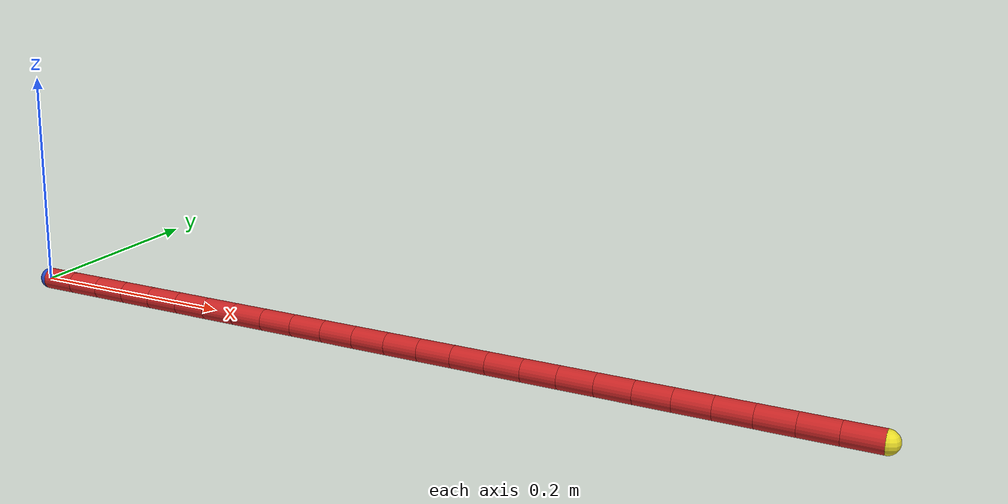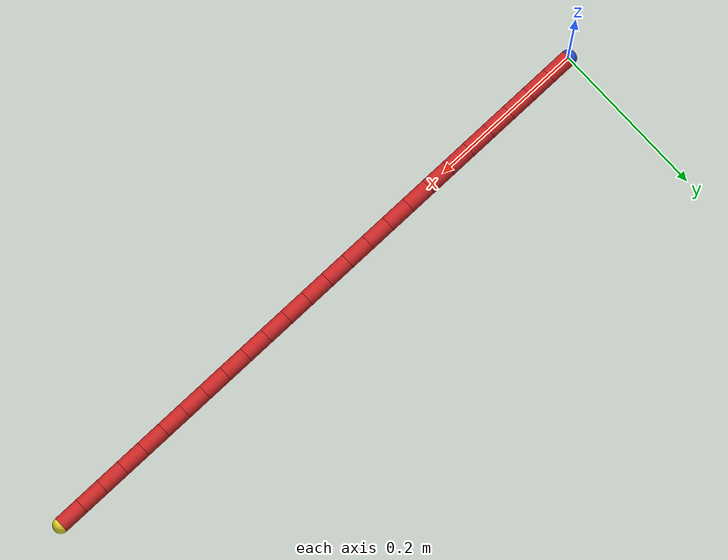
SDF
<sdf version="1.6">
    <model name="rope_3d">
        <allow_auto_disable>true</allow_auto_disable>
        <pose frame="">0 0 0 0 0 0</pose>

        <link name="rope_link_1">
            <pose frame="">0.016 0 0 3.14159 -1.57079 3.14159</pose>
            <inertial>
                <pose frame="">0 0 0 0 0 0</pose>
                <mass>0.008
                </mass>
                <inertia>
                    <ixx>8.826666666666665e-07
                    </ixx>
                    <ixy>0</ixy>
                    <ixz>0</ixz>
                    <iyy>8.826666666666665e-07
                    </iyy>
                    <iyz>0</iyz>
                    <izz>4.0000000000000003e-07
                    </izz>
                </inertia>
            </inertial>
            <collision name="link_1_collision">
                <max_contacts>2</max_contacts>
                <pose frame="">0 0 0 0 0 0</pose>
                <geometry>
                    <cylinder>
                        <length>0.032</length>
                        <radius>0.01</radius>
                    </cylinder>
                </geometry>
                <surface>
                    <friction>
                        <ode>
                            <mu>10.00</mu>
                            <mu2>10.00</mu2>
                        </ode>
                    </friction>
                    <contact>
                        <ode>
                            <kp>1e15</kp>
                            <kd>1e11</kd>
                        </ode>
                    </contact>
                </surface>
            </collision>

            <collision name="link_1_collision_ball1">
                <max_contacts>2</max_contacts>
                <pose frame="">0 0 0.016 0 0 0</pose>
                <geometry>
                    <sphere>
                        <radius>0.01</radius>
                    </sphere>
                </geometry>
                <surface>
                    <friction>
                        <ode>
                            <mu>1.00</mu>
                            <mu2>1.00</mu2>
                        </ode>
                    </friction>
                    <contact>
                        <ode>
                            <kp>1e15</kp>
                            <kd>1e11</kd>
                        </ode>
                    </contact>
                </surface>
            </collision>

            <collision name="link_1_collision_ball2">
                <max_contacts>2</max_contacts>
                <pose frame="">0 0 -0.016 0 0 0</pose>
                <geometry>
                    <sphere>
                        <radius>0.01</radius>
                    </sphere>
                </geometry>
                <surface>
                    <friction>
                        <ode>
                            <mu>1.00</mu>
                            <mu2>1.00</mu2>
                        </ode>
                    </friction>
                    <contact>
                        <ode>
                            <kp>1e15</kp>
                            <kd>1e11</kd>
                        </ode>
                    </contact>
                </surface>
            </collision>

            <visual name="link_1_visual">
                <cast_shadows>0</cast_shadows>
                <pose frame="">0 0 0 0 0 0</pose>
                <geometry>
                    <cylinder>
                        <length>0.032
                        </length>
                        <radius>0.01
                        </radius>
                    </cylinder>
                </geometry>
                <material>
                    <script>
                        <name>Gazebo/Red</name>
                        <uri>file://media/materials/scripts/gazebo.material</uri>
                    </script>
                </material>
            </visual>
            <self_collide>1</self_collide>
        </link>

        <link name="rope_link_2">
            <pose frame="">0.048 0 0 3.14159 -1.57079 3.14159</pose>
            <inertial>
                <pose frame="">0 0 0 0 0 0</pose>
                <mass>0.008
                </mass>
                <inertia>
                    <ixx>8.826666666666665e-07
                    </ixx>
                    <ixy>0</ixy>
                    <ixz>0</ixz>
                    <iyy>8.826666666666665e-07
                    </iyy>
                    <iyz>0</iyz>
                    <izz>4.0000000000000003e-07
                    </izz>
                </inertia>
            </inertial>
            <collision name="link_2_collision">
                <max_contacts>2</max_contacts>
                <pose frame="">0 0 0 0 0 0</pose>
                <geometry>
                    <cylinder>
                        <length>0.032</length>
                        <radius>0.01</radius>
                    </cylinder>
                </geometry>
                <surface>
                    <friction>
                        <ode>
                            <mu>10.00</mu>
                            <mu2>10.00</mu2>
                        </ode>
                    </friction>
                    <contact>
                        <ode>
                            <kp>1e15</kp>
                            <kd>1e11</kd>
                        </ode>
                    </contact>
                </surface>
            </collision>

            <collision name="link_2_collision_ball1">
                <max_contacts>2</max_contacts>
                <pose frame="">0 0 0.016 0 0 0</pose>
                <geometry>
                    <sphere>
                        <radius>0.01</radius>
                    </sphere>
                </geometry>
                <surface>
                    <friction>
                        <ode>
                            <mu>1.00</mu>
                            <mu2>1.00</mu2>
                        </ode>
                    </friction>
                    <contact>
                        <ode>
                            <kp>1e15</kp>
                            <kd>1e11</kd>
                        </ode>
                    </contact>
                </surface>
            </collision>

            <collision name="link_2_collision_ball2">
                <max_contacts>2</max_contacts>
                <pose frame="">0 0 -0.016 0 0 0</pose>
                <geometry>
                    <sphere>
                        <radius>0.01</radius>
                    </sphere>
                </geometry>
                <surface>
                    <friction>
                        <ode>
                            <mu>1.00</mu>
                            <mu2>1.00</mu2>
                        </ode>
                    </friction>
                    <contact>
                        <ode>
                            <kp>1e15</kp>
                            <kd>1e11</kd>
                        </ode>
                    </contact>
                </surface>
            </collision>

            <visual name="link_2_visual">
                <cast_shadows>0</cast_shadows>
                <pose frame="">0 0 0 0 0 0</pose>
                <geometry>
                    <cylinder>
                        <length>0.032
                        </length>
                        <radius>0.01
                        </radius>
                    </cylinder>
                </geometry>
                <material>
                    <script>
                        <name>Gazebo/Red</name>
                        <uri>file://media/materials/scripts/gazebo.material</uri>
                    </script>
                </material>
            </visual>
            <self_collide>1</self_collide>
        </link>

        <link name="rope_link_3">
            <pose frame="">0.08 0 0 3.14159 -1.57079 3.14159</pose>
            <inertial>
                <pose frame="">0 0 0 0 0 0</pose>
                <mass>0.008
                </mass>
                <inertia>
                    <ixx>8.826666666666665e-07
                    </ixx>
                    <ixy>0</ixy>
                    <ixz>0</ixz>
                    <iyy>8.826666666666665e-07
                    </iyy>
                    <iyz>0</iyz>
                    <izz>4.0000000000000003e-07
                    </izz>
                </inertia>
            </inertial>
            <collision name="link_3_collision">
                <max_contacts>2</max_contacts>
                <pose frame="">0 0 0 0 0 0</pose>
                <geometry>
                    <cylinder>
                        <length>0.032</length>
                        <radius>0.01</radius>
                    </cylinder>
                </geometry>
                <surface>
                    <friction>
                        <ode>
                            <mu>10.00</mu>
                            <mu2>10.00</mu2>
                        </ode>
                    </friction>
                    <contact>
                        <ode>
                            <kp>1e15</kp>
                            <kd>1e11</kd>
                        </ode>
                    </contact>
                </surface>
            </collision>

            <collision name="link_3_collision_ball1">
                <max_contacts>2</max_contacts>
                <pose frame="">0 0 0.016 0 0 0</pose>
                <geometry>
                    <sphere>
                        <radius>0.01</radius>
                    </sphere>
                </geometry>
                <surface>
                    <friction>
                        <ode>
                            <mu>1.00</mu>
                            <mu2>1.00</mu2>
                        </ode>
                    </friction>
                    <contact>
                        <ode>
                            <kp>1e15</kp>
                            <kd>1e11</kd>
                        </ode>
                    </contact>
                </surface>
            </collision>

            <collision name="link_3_collision_ball2">
                <max_contacts>2</max_contacts>
                <pose frame="">0 0 -0.016 0 0 0</pose>
                <geometry>
                    <sphere>
                        <radius>0.01</radius>
                    </sphere>
                </geometry>
                <surface>
                    <friction>
                        <ode>
                            <mu>1.00</mu>
                            <mu2>1.00</mu2>
                        </ode>
                    </friction>
                    <contact>
                        <ode>
                            <kp>1e15</kp>
                            <kd>1e11</kd>
                        </ode>
                    </contact>
                </surface>
            </collision>

            <visual name="link_3_visual">
                <cast_shadows>0</cast_shadows>
                <pose frame="">0 0 0 0 0 0</pose>
                <geometry>
                    <cylinder>
                        <length>0.032
                        </length>
                        <radius>0.01
                        </radius>
                    </cylinder>
                </geometry>
                <material>
                    <script>
                        <name>Gazebo/Red</name>
                        <uri>file://media/materials/scripts/gazebo.material</uri>
                    </script>
                </material>
            </visual>
            <self_collide>1</self_collide>
        </link>

        <link name="rope_link_4">
            <pose frame="">0.112 0 0 3.14159 -1.57079 3.14159</pose>
            <inertial>
                <pose frame="">0 0 0 0 0 0</pose>
                <mass>0.008
                </mass>
                <inertia>
                    <ixx>8.826666666666665e-07
                    </ixx>
                    <ixy>0</ixy>
                    <ixz>0</ixz>
                    <iyy>8.826666666666665e-07
                    </iyy>
                    <iyz>0</iyz>
                    <izz>4.0000000000000003e-07
                    </izz>
                </inertia>
            </inertial>
            <collision name="link_4_collision">
                <max_contacts>2</max_contacts>
                <pose frame="">0 0 0 0 0 0</pose>
                <geometry>
                    <cylinder>
                        <length>0.032</length>
                        <radius>0.01</radius>
                    </cylinder>
                </geometry>
                <surface>
                    <friction>
                        <ode>
                            <mu>10.00</mu>
                            <mu2>10.00</mu2>
                        </ode>
                    </friction>
                    <contact>
                        <ode>
                            <kp>1e15</kp>
                            <kd>1e11</kd>
                        </ode>
                    </contact>
                </surface>
            </collision>

            <collision name="link_4_collision_ball1">
                <max_contacts>2</max_contacts>
                <pose frame="">0 0 0.016 0 0 0</pose>
                <geometry>
                    <sphere>
                        <radius>0.01</radius>
                    </sphere>
                </geometry>
                <surface>
                    <friction>
                        <ode>
                            <mu>1.00</mu>
                            <mu2>1.00</mu2>
                        </ode>
                    </friction>
                    <contact>
                        <ode>
                            <kp>1e15</kp>
                            <kd>1e11</kd>
                        </ode>
                    </contact>
                </surface>
            </collision>

            <collision name="link_4_collision_ball2">
                <max_contacts>2</max_contacts>
                <pose frame="">0 0 -0.016 0 0 0</pose>
                <geometry>
                    <sphere>
                        <radius>0.01</radius>
                    </sphere>
                </geometry>
                <surface>
                    <friction>
                        <ode>
                            <mu>1.00</mu>
                            <mu2>1.00</mu2>
                        </ode>
                    </friction>
                    <contact>
                        <ode>
                            <kp>1e15</kp>
                            <kd>1e11</kd>
                        </ode>
                    </contact>
                </surface>
            </collision>

            <visual name="link_4_visual">
                <cast_shadows>0</cast_shadows>
                <pose frame="">0 0 0 0 0 0</pose>
                <geometry>
                    <cylinder>
                        <length>0.032
                        </length>
                        <radius>0.01
                        </radius>
                    </cylinder>
                </geometry>
                <material>
                    <script>
                        <name>Gazebo/Red</name>
                        <uri>file://media/materials/scripts/gazebo.material</uri>
                    </script>
                </material>
            </visual>
            <self_collide>1</self_collide>
        </link>

        <link name="rope_link_5">
            <pose frame="">0.14400000000000002 0 0 3.14159 -1.57079 3.14159</pose>
            <inertial>
                <pose frame="">0 0 0 0 0 0</pose>
                <mass>0.008
                </mass>
                <inertia>
                    <ixx>8.826666666666665e-07
                    </ixx>
                    <ixy>0</ixy>
                    <ixz>0</ixz>
                    <iyy>8.826666666666665e-07
                    </iyy>
                    <iyz>0</iyz>
                    <izz>4.0000000000000003e-07
                    </izz>
                </inertia>
            </inertial>
            <collision name="link_5_collision">
                <max_contacts>2</max_contacts>
                <pose frame="">0 0 0 0 0 0</pose>
                <geometry>
                    <cylinder>
                        <length>0.032</length>
                        <radius>0.01</radius>
                    </cylinder>
                </geometry>
                <surface>
                    <friction>
                        <ode>
                            <mu>10.00</mu>
                            <mu2>10.00</mu2>
                        </ode>
                    </friction>
                    <contact>
                        <ode>
                            <kp>1e15</kp>
                            <kd>1e11</kd>
                        </ode>
                    </contact>
                </surface>
            </collision>

            <collision name="link_5_collision_ball1">
                <max_contacts>2</max_contacts>
                <pose frame="">0 0 0.016 0 0 0</pose>
                <geometry>
                    <sphere>
                        <radius>0.01</radius>
                    </sphere>
                </geometry>
                <surface>
                    <friction>
                        <ode>
                            <mu>1.00</mu>
                            <mu2>1.00</mu2>
                        </ode>
                    </friction>
                    <contact>
                        <ode>
                            <kp>1e15</kp>
                            <kd>1e11</kd>
                        </ode>
                    </contact>
                </surface>
            </collision>

            <collision name="link_5_collision_ball2">
                <max_contacts>2</max_contacts>
                <pose frame="">0 0 -0.016 0 0 0</pose>
                <geometry>
                    <sphere>
                        <radius>0.01</radius>
                    </sphere>
                </geometry>
                <surface>
                    <friction>
                        <ode>
                            <mu>1.00</mu>
                            <mu2>1.00</mu2>
                        </ode>
                    </friction>
                    <contact>
                        <ode>
                            <kp>1e15</kp>
                            <kd>1e11</kd>
                        </ode>
                    </contact>
                </surface>
            </collision>

            <visual name="link_5_visual">
                <cast_shadows>0</cast_shadows>
                <pose frame="">0 0 0 0 0 0</pose>
                <geometry>
                    <cylinder>
                        <length>0.032
                        </length>
                        <radius>0.01
                        </radius>
                    </cylinder>
                </geometry>
                <material>
                    <script>
                        <name>Gazebo/Red</name>
                        <uri>file://media/materials/scripts/gazebo.material</uri>
                    </script>
                </material>
            </visual>
            <self_collide>1</self_collide>
        </link>

        <link name="rope_link_6">
            <pose frame="">0.176 0 0 3.14159 -1.57079 3.14159</pose>
            <inertial>
                <pose frame="">0 0 0 0 0 0</pose>
                <mass>0.008
                </mass>
                <inertia>
                    <ixx>8.826666666666665e-07
                    </ixx>
                    <ixy>0</ixy>
                    <ixz>0</ixz>
                    <iyy>8.826666666666665e-07
                    </iyy>
                    <iyz>0</iyz>
                    <izz>4.0000000000000003e-07
                    </izz>
                </inertia>
            </inertial>
            <collision name="link_6_collision">
                <max_contacts>2</max_contacts>
                <pose frame="">0 0 0 0 0 0</pose>
                <geometry>
                    <cylinder>
                        <length>0.032</length>
                        <radius>0.01</radius>
                    </cylinder>
                </geometry>
                <surface>
                    <friction>
                        <ode>
                            <mu>10.00</mu>
                            <mu2>10.00</mu2>
                        </ode>
                    </friction>
                    <contact>
                        <ode>
                            <kp>1e15</kp>
                            <kd>1e11</kd>
                        </ode>
                    </contact>
                </surface>
            </collision>

            <collision name="link_6_collision_ball1">
                <max_contacts>2</max_contacts>
                <pose frame="">0 0 0.016 0 0 0</pose>
                <geometry>
                    <sphere>
                        <radius>0.01</radius>
                    </sphere>
                </geometry>
                <surface>
                    <friction>
                        <ode>
                            <mu>1.00</mu>
                            <mu2>1.00</mu2>
                        </ode>
                    </friction>
                    <contact>
                        <ode>
                            <kp>1e15</kp>
                            <kd>1e11</kd>
                        </ode>
                    </contact>
                </surface>
            </collision>

            <collision name="link_6_collision_ball2">
                <max_contacts>2</max_contacts>
                <pose frame="">0 0 -0.016 0 0 0</pose>
                <geometry>
                    <sphere>
                        <radius>0.01</radius>
                    </sphere>
                </geometry>
                <surface>
                    <friction>
                        <ode>
                            <mu>1.00</mu>
                            <mu2>1.00</mu2>
                        </ode>
                    </friction>
                    <contact>
                        <ode>
                            <kp>1e15</kp>
                            <kd>1e11</kd>
                        </ode>
                    </contact>
                </surface>
            </collision>

            <visual name="link_6_visual">
                <cast_shadows>0</cast_shadows>
                <pose frame="">0 0 0 0 0 0</pose>
                <geometry>
                    <cylinder>
                        <length>0.032
                        </length>
                        <radius>0.01
                        </radius>
                    </cylinder>
                </geometry>
                <material>
                    <script>
                        <name>Gazebo/Red</name>
                        <uri>file://media/materials/scripts/gazebo.material</uri>
                    </script>
                </material>
            </visual>
            <self_collide>1</self_collide>
        </link>

        <link name="rope_link_7">
            <pose frame="">0.20800000000000002 0 0 3.14159 -1.57079 3.14159</pose>
            <inertial>
                <pose frame="">0 0 0 0 0 0</pose>
                <mass>0.008
                </mass>
                <inertia>
                    <ixx>8.826666666666665e-07
                    </ixx>
                    <ixy>0</ixy>
                    <ixz>0</ixz>
                    <iyy>8.826666666666665e-07
                    </iyy>
                    <iyz>0</iyz>
                    <izz>4.0000000000000003e-07
                    </izz>
                </inertia>
            </inertial>
            <collision name="link_7_collision">
                <max_contacts>2</max_contacts>
                <pose frame="">0 0 0 0 0 0</pose>
                <geometry>
                    <cylinder>
                        <length>0.032</length>
                        <radius>0.01</radius>
                    </cylinder>
                </geometry>
                <surface>
                    <friction>
                        <ode>
                            <mu>10.00</mu>
                            <mu2>10.00</mu2>
                        </ode>
                    </friction>
                    <contact>
                        <ode>
                            <kp>1e15</kp>
                            <kd>1e11</kd>
                        </ode>
                    </contact>
                </surface>
            </collision>

            <collision name="link_7_collision_ball1">
                <max_contacts>2</max_contacts>
                <pose frame="">0 0 0.016 0 0 0</pose>
                <geometry>
                    <sphere>
                        <radius>0.01</radius>
                    </sphere>
                </geometry>
                <surface>
                    <friction>
                        <ode>
                            <mu>1.00</mu>
                            <mu2>1.00</mu2>
                        </ode>
                    </friction>
                    <contact>
                        <ode>
                            <kp>1e15</kp>
                            <kd>1e11</kd>
                        </ode>
                    </contact>
                </surface>
            </collision>

            <collision name="link_7_collision_ball2">
                <max_contacts>2</max_contacts>
                <pose frame="">0 0 -0.016 0 0 0</pose>
                <geometry>
                    <sphere>
                        <radius>0.01</radius>
                    </sphere>
                </geometry>
                <surface>
                    <friction>
                        <ode>
                            <mu>1.00</mu>
                            <mu2>1.00</mu2>
                        </ode>
                    </friction>
                    <contact>
                        <ode>
                            <kp>1e15</kp>
                            <kd>1e11</kd>
                        </ode>
                    </contact>
                </surface>
            </collision>

            <visual name="link_7_visual">
                <cast_shadows>0</cast_shadows>
                <pose frame="">0 0 0 0 0 0</pose>
                <geometry>
                    <cylinder>
                        <length>0.032
                        </length>
                        <radius>0.01
                        </radius>
                    </cylinder>
                </geometry>
                <material>
                    <script>
                        <name>Gazebo/Red</name>
                        <uri>file://media/materials/scripts/gazebo.material</uri>
                    </script>
                </material>
            </visual>
            <self_collide>1</self_collide>
        </link>

        <link name="rope_link_8">
            <pose frame="">0.24 0 0 3.14159 -1.57079 3.14159</pose>
            <inertial>
                <pose frame="">0 0 0 0 0 0</pose>
                <mass>0.008
                </mass>
                <inertia>
                    <ixx>8.826666666666665e-07
                    </ixx>
                    <ixy>0</ixy>
                    <ixz>0</ixz>
                    <iyy>8.826666666666665e-07
                    </iyy>
                    <iyz>0</iyz>
                    <izz>4.0000000000000003e-07
                    </izz>
                </inertia>
            </inertial>
            <collision name="link_8_collision">
                <max_contacts>2</max_contacts>
                <pose frame="">0 0 0 0 0 0</pose>
                <geometry>
                    <cylinder>
                        <length>0.032</length>
                        <radius>0.01</radius>
                    </cylinder>
                </geometry>
                <surface>
                    <friction>
                        <ode>
                            <mu>10.00</mu>
                            <mu2>10.00</mu2>
                        </ode>
                    </friction>
                    <contact>
                        <ode>
                            <kp>1e15</kp>
                            <kd>1e11</kd>
                        </ode>
                    </contact>
                </surface>
            </collision>

            <collision name="link_8_collision_ball1">
                <max_contacts>2</max_contacts>
                <pose frame="">0 0 0.016 0 0 0</pose>
                <geometry>
                    <sphere>
                        <radius>0.01</radius>
                    </sphere>
                </geometry>
                <surface>
                    <friction>
                        <ode>
                            <mu>1.00</mu>
                            <mu2>1.00</mu2>
                        </ode>
                    </friction>
                    <contact>
                        <ode>
                            <kp>1e15</kp>
                            <kd>1e11</kd>
                        </ode>
                    </contact>
                </surface>
            </collision>

            <collision name="link_8_collision_ball2">
                <max_contacts>2</max_contacts>
                <pose frame="">0 0 -0.016 0 0 0</pose>
                <geometry>
                    <sphere>
                        <radius>0.01</radius>
                    </sphere>
                </geometry>
                <surface>
                    <friction>
                        <ode>
                            <mu>1.00</mu>
                            <mu2>1.00</mu2>
                        </ode>
                    </friction>
                    <contact>
                        <ode>
                            <kp>1e15</kp>
                            <kd>1e11</kd>
                        </ode>
                    </contact>
                </surface>
            </collision>

            <visual name="link_8_visual">
                <cast_shadows>0</cast_shadows>
                <pose frame="">0 0 0 0 0 0</pose>
                <geometry>
                    <cylinder>
                        <length>0.032
                        </length>
                        <radius>0.01
                        </radius>
                    </cylinder>
                </geometry>
                <material>
                    <script>
                        <name>Gazebo/Red</name>
                        <uri>file://media/materials/scripts/gazebo.material</uri>
                    </script>
                </material>
            </visual>
            <self_collide>1</self_collide>
        </link>

        <link name="rope_link_9">
            <pose frame="">0.272 0 0 3.14159 -1.57079 3.14159</pose>
            <inertial>
                <pose frame="">0 0 0 0 0 0</pose>
                <mass>0.008
                </mass>
                <inertia>
                    <ixx>8.826666666666665e-07
                    </ixx>
                    <ixy>0</ixy>
                    <ixz>0</ixz>
                    <iyy>8.826666666666665e-07
                    </iyy>
                    <iyz>0</iyz>
                    <izz>4.0000000000000003e-07
                    </izz>
                </inertia>
            </inertial>
            <collision name="link_9_collision">
                <max_contacts>2</max_contacts>
                <pose frame="">0 0 0 0 0 0</pose>
                <geometry>
                    <cylinder>
                        <length>0.032</length>
                        <radius>0.01</radius>
                    </cylinder>
                </geometry>
                <surface>
                    <friction>
                        <ode>
                            <mu>10.00</mu>
                            <mu2>10.00</mu2>
                        </ode>
                    </friction>
                    <contact>
                        <ode>
                            <kp>1e15</kp>
                            <kd>1e11</kd>
                        </ode>
                    </contact>
                </surface>
            </collision>

            <collision name="link_9_collision_ball1">
                <max_contacts>2</max_contacts>
                <pose frame="">0 0 0.016 0 0 0</pose>
                <geometry>
                    <sphere>
                        <radius>0.01</radius>
                    </sphere>
                </geometry>
                <surface>
                    <friction>
                        <ode>
                            <mu>1.00</mu>
                            <mu2>1.00</mu2>
                        </ode>
                    </friction>
                    <contact>
                        <ode>
                            <kp>1e15</kp>
                            <kd>1e11</kd>
                        </ode>
                    </contact>
                </surface>
            </collision>

            <collision name="link_9_collision_ball2">
                <max_contacts>2</max_contacts>
                <pose frame="">0 0 -0.016 0 0 0</pose>
                <geometry>
                    <sphere>
                        <radius>0.01</radius>
                    </sphere>
                </geometry>
                <surface>
                    <friction>
                        <ode>
                            <mu>1.00</mu>
                            <mu2>1.00</mu2>
                        </ode>
                    </friction>
                    <contact>
                        <ode>
                            <kp>1e15</kp>
                            <kd>1e11</kd>
                        </ode>
                    </contact>
                </surface>
            </collision>

            <visual name="link_9_visual">
                <cast_shadows>0</cast_shadows>
                <pose frame="">0 0 0 0 0 0</pose>
                <geometry>
                    <cylinder>
                        <length>0.032
                        </length>
                        <radius>0.01
                        </radius>
                    </cylinder>
                </geometry>
                <material>
                    <script>
                        <name>Gazebo/Red</name>
                        <uri>file://media/materials/scripts/gazebo.material</uri>
                    </script>
                </material>
            </visual>
            <self_collide>1</self_collide>
        </link>

        <link name="rope_link_10">
            <pose frame="">0.30400000000000005 0 0 3.14159 -1.57079 3.14159</pose>
            <inertial>
                <pose frame="">0 0 0 0 0 0</pose>
                <mass>0.008
                </mass>
                <inertia>
                    <ixx>8.826666666666665e-07
                    </ixx>
                    <ixy>0</ixy>
                    <ixz>0</ixz>
                    <iyy>8.826666666666665e-07
                    </iyy>
                    <iyz>0</iyz>
                    <izz>4.0000000000000003e-07
                    </izz>
                </inertia>
            </inertial>
            <collision name="link_10_collision">
                <max_contacts>2</max_contacts>
                <pose frame="">0 0 0 0 0 0</pose>
                <geometry>
                    <cylinder>
                        <length>0.032</length>
                        <radius>0.01</radius>
                    </cylinder>
                </geometry>
                <surface>
                    <friction>
                        <ode>
                            <mu>10.00</mu>
                            <mu2>10.00</mu2>
                        </ode>
                    </friction>
                    <contact>
                        <ode>
                            <kp>1e15</kp>
                            <kd>1e11</kd>
                        </ode>
                    </contact>
                </surface>
            </collision>

            <collision name="link_10_collision_ball1">
                <max_contacts>2</max_contacts>
                <pose frame="">0 0 0.016 0 0 0</pose>
                <geometry>
                    <sphere>
                        <radius>0.01</radius>
                    </sphere>
                </geometry>
                <surface>
                    <friction>
                        <ode>
                            <mu>1.00</mu>
                            <mu2>1.00</mu2>
                        </ode>
                    </friction>
                    <contact>
                        <ode>
                            <kp>1e15</kp>
                            <kd>1e11</kd>
                        </ode>
                    </contact>
                </surface>
            </collision>

            <collision name="link_10_collision_ball2">
                <max_contacts>2</max_contacts>
                <pose frame="">0 0 -0.016 0 0 0</pose>
                <geometry>
                    <sphere>
                        <radius>0.01</radius>
                    </sphere>
                </geometry>
                <surface>
                    <friction>
                        <ode>
                            <mu>1.00</mu>
                            <mu2>1.00</mu2>
                        </ode>
                    </friction>
                    <contact>
                        <ode>
                            <kp>1e15</kp>
                            <kd>1e11</kd>
                        </ode>
                    </contact>
                </surface>
            </collision>

            <visual name="link_10_visual">
                <cast_shadows>0</cast_shadows>
                <pose frame="">0 0 0 0 0 0</pose>
                <geometry>
                    <cylinder>
                        <length>0.032
                        </length>
                        <radius>0.01
                        </radius>
                    </cylinder>
                </geometry>
                <material>
                    <script>
                        <name>Gazebo/Red</name>
                        <uri>file://media/materials/scripts/gazebo.material</uri>
                    </script>
                </material>
            </visual>
            <self_collide>1</self_collide>
        </link>

        <link name="rope_link_11">
            <pose frame="">0.336 0 0 3.14159 -1.57079 3.14159</pose>
            <inertial>
                <pose frame="">0 0 0 0 0 0</pose>
                <mass>0.008
                </mass>
                <inertia>
                    <ixx>8.826666666666665e-07
                    </ixx>
                    <ixy>0</ixy>
                    <ixz>0</ixz>
                    <iyy>8.826666666666665e-07
                    </iyy>
                    <iyz>0</iyz>
                    <izz>4.0000000000000003e-07
                    </izz>
                </inertia>
            </inertial>
            <collision name="link_11_collision">
                <max_contacts>2</max_contacts>
                <pose frame="">0 0 0 0 0 0</pose>
                <geometry>
                    <cylinder>
                        <length>0.032</length>
                        <radius>0.01</radius>
                    </cylinder>
                </geometry>
                <surface>
                    <friction>
                        <ode>
                            <mu>10.00</mu>
                            <mu2>10.00</mu2>
                        </ode>
                    </friction>
                    <contact>
                        <ode>
                            <kp>1e15</kp>
                            <kd>1e11</kd>
                        </ode>
                    </contact>
                </surface>
            </collision>

            <collision name="link_11_collision_ball1">
                <max_contacts>2</max_contacts>
                <pose frame="">0 0 0.016 0 0 0</pose>
                <geometry>
                    <sphere>
                        <radius>0.01</radius>
                    </sphere>
                </geometry>
                <surface>
                    <friction>
                        <ode>
                            <mu>1.00</mu>
                            <mu2>1.00</mu2>
                        </ode>
                    </friction>
                    <contact>
                        <ode>
                            <kp>1e15</kp>
                            <kd>1e11</kd>
                        </ode>
                    </contact>
                </surface>
            </collision>

            <collision name="link_11_collision_ball2">
                <max_contacts>2</max_contacts>
                <pose frame="">0 0 -0.016 0 0 0</pose>
                <geometry>
                    <sphere>
                        <radius>0.01</radius>
                    </sphere>
                </geometry>
                <surface>
                    <friction>
                        <ode>
                            <mu>1.00</mu>
                            <mu2>1.00</mu2>
                        </ode>
                    </friction>
                    <contact>
                        <ode>
                            <kp>1e15</kp>
                            <kd>1e11</kd>
                        </ode>
                    </contact>
                </surface>
            </collision>

            <visual name="link_11_visual">
                <cast_shadows>0</cast_shadows>
                <pose frame="">0 0 0 0 0 0</pose>
                <geometry>
                    <cylinder>
                        <length>0.032
                        </length>
                        <radius>0.01
                        </radius>
                    </cylinder>
                </geometry>
                <material>
                    <script>
                        <name>Gazebo/Red</name>
                        <uri>file://media/materials/scripts/gazebo.material</uri>
                    </script>
                </material>
            </visual>
            <self_collide>1</self_collide>
        </link>

        <link name="rope_link_12">
            <pose frame="">0.368 0 0 3.14159 -1.57079 3.14159</pose>
            <inertial>
                <pose frame="">0 0 0 0 0 0</pose>
                <mass>0.008
                </mass>
                <inertia>
                    <ixx>8.826666666666665e-07
                    </ixx>
                    <ixy>0</ixy>
                    <ixz>0</ixz>
                    <iyy>8.826666666666665e-07
                    </iyy>
                    <iyz>0</iyz>
                    <izz>4.0000000000000003e-07
                    </izz>
                </inertia>
            </inertial>
            <collision name="link_12_collision">
                <max_contacts>2</max_contacts>
                <pose frame="">0 0 0 0 0 0</pose>
                <geometry>
                    <cylinder>
                        <length>0.032</length>
                        <radius>0.01</radius>
                    </cylinder>
                </geometry>
                <surface>
                    <friction>
                        <ode>
                            <mu>10.00</mu>
                            <mu2>10.00</mu2>
                        </ode>
                    </friction>
                    <contact>
                        <ode>
                            <kp>1e15</kp>
                            <kd>1e11</kd>
                        </ode>
                    </contact>
                </surface>
            </collision>

            <collision name="link_12_collision_ball1">
                <max_contacts>2</max_contacts>
                <pose frame="">0 0 0.016 0 0 0</pose>
                <geometry>
                    <sphere>
                        <radius>0.01</radius>
                    </sphere>
                </geometry>
                <surface>
                    <friction>
                        <ode>
                            <mu>1.00</mu>
                            <mu2>1.00</mu2>
                        </ode>
                    </friction>
                    <contact>
                        <ode>
                            <kp>1e15</kp>
                            <kd>1e11</kd>
                        </ode>
                    </contact>
                </surface>
            </collision>

            <collision name="link_12_collision_ball2">
                <max_contacts>2</max_contacts>
                <pose frame="">0 0 -0.016 0 0 0</pose>
                <geometry>
                    <sphere>
                        <radius>0.01</radius>
                    </sphere>
                </geometry>
                <surface>
                    <friction>
                        <ode>
                            <mu>1.00</mu>
                            <mu2>1.00</mu2>
                        </ode>
                    </friction>
                    <contact>
                        <ode>
                            <kp>1e15</kp>
                            <kd>1e11</kd>
                        </ode>
                    </contact>
                </surface>
            </collision>

            <visual name="link_12_visual">
                <cast_shadows>0</cast_shadows>
                <pose frame="">0 0 0 0 0 0</pose>
                <geometry>
                    <cylinder>
                        <length>0.032
                        </length>
                        <radius>0.01
                        </radius>
                    </cylinder>
                </geometry>
                <material>
                    <script>
                        <name>Gazebo/Red</name>
                        <uri>file://media/materials/scripts/gazebo.material</uri>
                    </script>
                </material>
            </visual>
            <self_collide>1</self_collide>
        </link>

        <link name="rope_link_13">
            <pose frame="">0.4 0 0 3.14159 -1.57079 3.14159</pose>
            <inertial>
                <pose frame="">0 0 0 0 0 0</pose>
                <mass>0.008
                </mass>
                <inertia>
                    <ixx>8.826666666666665e-07
                    </ixx>
                    <ixy>0</ixy>
                    <ixz>0</ixz>
                    <iyy>8.826666666666665e-07
                    </iyy>
                    <iyz>0</iyz>
                    <izz>4.0000000000000003e-07
                    </izz>
                </inertia>
            </inertial>
            <collision name="link_13_collision">
                <max_contacts>2</max_contacts>
                <pose frame="">0 0 0 0 0 0</pose>
                <geometry>
                    <cylinder>
                        <length>0.032</length>
                        <radius>0.01</radius>
                    </cylinder>
                </geometry>
                <surface>
                    <friction>
                        <ode>
                            <mu>10.00</mu>
                            <mu2>10.00</mu2>
                        </ode>
                    </friction>
                    <contact>
                        <ode>
                            <kp>1e15</kp>
                            <kd>1e11</kd>
                        </ode>
                    </contact>
                </surface>
            </collision>

            <collision name="link_13_collision_ball1">
                <max_contacts>2</max_contacts>
                <pose frame="">0 0 0.016 0 0 0</pose>
                <geometry>
                    <sphere>
                        <radius>0.01</radius>
                    </sphere>
                </geometry>
                <surface>
                    <friction>
                        <ode>
                            <mu>1.00</mu>
                            <mu2>1.00</mu2>
                        </ode>
                    </friction>
                    <contact>
                        <ode>
                            <kp>1e15</kp>
                            <kd>1e11</kd>
                        </ode>
                    </contact>
                </surface>
            </collision>

            <collision name="link_13_collision_ball2">
                <max_contacts>2</max_contacts>
                <pose frame="">0 0 -0.016 0 0 0</pose>
                <geometry>
                    <sphere>
                        <radius>0.01</radius>
                    </sphere>
                </geometry>
                <surface>
                    <friction>
                        <ode>
                            <mu>1.00</mu>
                            <mu2>1.00</mu2>
                        </ode>
                    </friction>
                    <contact>
                        <ode>
                            <kp>1e15</kp>
                            <kd>1e11</kd>
                        </ode>
                    </contact>
                </surface>
            </collision>

            <visual name="link_13_visual">
                <cast_shadows>0</cast_shadows>
                <pose frame="">0 0 0 0 0 0</pose>
                <geometry>
                    <cylinder>
                        <length>0.032
                        </length>
                        <radius>0.01
                        </radius>
                    </cylinder>
                </geometry>
                <material>
                    <script>
                        <name>Gazebo/Red</name>
                        <uri>file://media/materials/scripts/gazebo.material</uri>
                    </script>
                </material>
            </visual>
            <self_collide>1</self_collide>
        </link>

        <link name="rope_link_14">
            <pose frame="">0.43200000000000005 0 0 3.14159 -1.57079 3.14159</pose>
            <inertial>
                <pose frame="">0 0 0 0 0 0</pose>
                <mass>0.008
                </mass>
                <inertia>
                    <ixx>8.826666666666665e-07
                    </ixx>
                    <ixy>0</ixy>
                    <ixz>0</ixz>
                    <iyy>8.826666666666665e-07
                    </iyy>
                    <iyz>0</iyz>
                    <izz>4.0000000000000003e-07
                    </izz>
                </inertia>
            </inertial>
            <collision name="link_14_collision">
                <max_contacts>2</max_contacts>
                <pose frame="">0 0 0 0 0 0</pose>
                <geometry>
                    <cylinder>
                        <length>0.032</length>
                        <radius>0.01</radius>
                    </cylinder>
                </geometry>
                <surface>
                    <friction>
                        <ode>
                            <mu>10.00</mu>
                            <mu2>10.00</mu2>
                        </ode>
                    </friction>
                    <contact>
                        <ode>
                            <kp>1e15</kp>
                            <kd>1e11</kd>
                        </ode>
                    </contact>
                </surface>
            </collision>

            <collision name="link_14_collision_ball1">
                <max_contacts>2</max_contacts>
                <pose frame="">0 0 0.016 0 0 0</pose>
                <geometry>
                    <sphere>
                        <radius>0.01</radius>
                    </sphere>
                </geometry>
                <surface>
                    <friction>
                        <ode>
                            <mu>1.00</mu>
                            <mu2>1.00</mu2>
                        </ode>
                    </friction>
                    <contact>
                        <ode>
                            <kp>1e15</kp>
                            <kd>1e11</kd>
                        </ode>
                    </contact>
                </surface>
            </collision>

            <collision name="link_14_collision_ball2">
                <max_contacts>2</max_contacts>
                <pose frame="">0 0 -0.016 0 0 0</pose>
                <geometry>
                    <sphere>
                        <radius>0.01</radius>
                    </sphere>
                </geometry>
                <surface>
                    <friction>
                        <ode>
                            <mu>1.00</mu>
                            <mu2>1.00</mu2>
                        </ode>
                    </friction>
                    <contact>
                        <ode>
                            <kp>1e15</kp>
                            <kd>1e11</kd>
                        </ode>
                    </contact>
                </surface>
            </collision>

            <visual name="link_14_visual">
                <cast_shadows>0</cast_shadows>
                <pose frame="">0 0 0 0 0 0</pose>
                <geometry>
                    <cylinder>
                        <length>0.032
                        </length>
                        <radius>0.01
                        </radius>
                    </cylinder>
                </geometry>
                <material>
                    <script>
                        <name>Gazebo/Red</name>
                        <uri>file://media/materials/scripts/gazebo.material</uri>
                    </script>
                </material>
            </visual>
            <self_collide>1</self_collide>
        </link>

        <link name="rope_link_15">
            <pose frame="">0.464 0 0 3.14159 -1.57079 3.14159</pose>
            <inertial>
                <pose frame="">0 0 0 0 0 0</pose>
                <mass>0.008
                </mass>
                <inertia>
                    <ixx>8.826666666666665e-07
                    </ixx>
                    <ixy>0</ixy>
                    <ixz>0</ixz>
                    <iyy>8.826666666666665e-07
                    </iyy>
                    <iyz>0</iyz>
                    <izz>4.0000000000000003e-07
                    </izz>
                </inertia>
            </inertial>
            <collision name="link_15_collision">
                <max_contacts>2</max_contacts>
                <pose frame="">0 0 0 0 0 0</pose>
                <geometry>
                    <cylinder>
                        <length>0.032</length>
                        <radius>0.01</radius>
                    </cylinder>
                </geometry>
                <surface>
                    <friction>
                        <ode>
                            <mu>10.00</mu>
                            <mu2>10.00</mu2>
                        </ode>
                    </friction>
                    <contact>
                        <ode>
                            <kp>1e15</kp>
                            <kd>1e11</kd>
                        </ode>
                    </contact>
                </surface>
            </collision>

            <collision name="link_15_collision_ball1">
                <max_contacts>2</max_contacts>
                <pose frame="">0 0 0.016 0 0 0</pose>
                <geometry>
                    <sphere>
                        <radius>0.01</radius>
                    </sphere>
                </geometry>
                <surface>
                    <friction>
                        <ode>
                            <mu>1.00</mu>
                            <mu2>1.00</mu2>
                        </ode>
                    </friction>
                    <contact>
                        <ode>
                            <kp>1e15</kp>
                            <kd>1e11</kd>
                        </ode>
                    </contact>
                </surface>
            </collision>

            <collision name="link_15_collision_ball2">
                <max_contacts>2</max_contacts>
                <pose frame="">0 0 -0.016 0 0 0</pose>
                <geometry>
                    <sphere>
                        <radius>0.01</radius>
                    </sphere>
                </geometry>
                <surface>
                    <friction>
                        <ode>
                            <mu>1.00</mu>
                            <mu2>1.00</mu2>
                        </ode>
                    </friction>
                    <contact>
                        <ode>
                            <kp>1e15</kp>
                            <kd>1e11</kd>
                        </ode>
                    </contact>
                </surface>
            </collision>

            <visual name="link_15_visual">
                <cast_shadows>0</cast_shadows>
                <pose frame="">0 0 0 0 0 0</pose>
                <geometry>
                    <cylinder>
                        <length>0.032
                        </length>
                        <radius>0.01
                        </radius>
                    </cylinder>
                </geometry>
                <material>
                    <script>
                        <name>Gazebo/Red</name>
                        <uri>file://media/materials/scripts/gazebo.material</uri>
                    </script>
                </material>
            </visual>
            <self_collide>1</self_collide>
        </link>

        <link name="rope_link_16">
            <pose frame="">0.496 0 0 3.14159 -1.57079 3.14159</pose>
            <inertial>
                <pose frame="">0 0 0 0 0 0</pose>
                <mass>0.008
                </mass>
                <inertia>
                    <ixx>8.826666666666665e-07
                    </ixx>
                    <ixy>0</ixy>
                    <ixz>0</ixz>
                    <iyy>8.826666666666665e-07
                    </iyy>
                    <iyz>0</iyz>
                    <izz>4.0000000000000003e-07
                    </izz>
                </inertia>
            </inertial>
            <collision name="link_16_collision">
                <max_contacts>2</max_contacts>
                <pose frame="">0 0 0 0 0 0</pose>
                <geometry>
                    <cylinder>
                        <length>0.032</length>
                        <radius>0.01</radius>
                    </cylinder>
                </geometry>
                <surface>
                    <friction>
                        <ode>
                            <mu>10.00</mu>
                            <mu2>10.00</mu2>
                        </ode>
                    </friction>
                    <contact>
                        <ode>
                            <kp>1e15</kp>
                            <kd>1e11</kd>
                        </ode>
                    </contact>
                </surface>
            </collision>

            <collision name="link_16_collision_ball1">
                <max_contacts>2</max_contacts>
                <pose frame="">0 0 0.016 0 0 0</pose>
                <geometry>
                    <sphere>
                        <radius>0.01</radius>
                    </sphere>
                </geometry>
                <surface>
                    <friction>
                        <ode>
                            <mu>1.00</mu>
                            <mu2>1.00</mu2>
                        </ode>
                    </friction>
                    <contact>
                        <ode>
                            <kp>1e15</kp>
                            <kd>1e11</kd>
                        </ode>
                    </contact>
                </surface>
            </collision>

            <collision name="link_16_collision_ball2">
                <max_contacts>2</max_contacts>
                <pose frame="">0 0 -0.016 0 0 0</pose>
                <geometry>
                    <sphere>
                        <radius>0.01</radius>
                    </sphere>
                </geometry>
                <surface>
                    <friction>
                        <ode>
                            <mu>1.00</mu>
                            <mu2>1.00</mu2>
                        </ode>
                    </friction>
                    <contact>
                        <ode>
                            <kp>1e15</kp>
                            <kd>1e11</kd>
                        </ode>
                    </contact>
                </surface>
            </collision>

            <visual name="link_16_visual">
                <cast_shadows>0</cast_shadows>
                <pose frame="">0 0 0 0 0 0</pose>
                <geometry>
                    <cylinder>
                        <length>0.032
                        </length>
                        <radius>0.01
                        </radius>
                    </cylinder>
                </geometry>
                <material>
                    <script>
                        <name>Gazebo/Red</name>
                        <uri>file://media/materials/scripts/gazebo.material</uri>
                    </script>
                </material>
            </visual>
            <self_collide>1</self_collide>
        </link>

        <link name="rope_link_17">
            <pose frame="">0.528 0 0 3.14159 -1.57079 3.14159</pose>
            <inertial>
                <pose frame="">0 0 0 0 0 0</pose>
                <mass>0.008
                </mass>
                <inertia>
                    <ixx>8.826666666666665e-07
                    </ixx>
                    <ixy>0</ixy>
                    <ixz>0</ixz>
                    <iyy>8.826666666666665e-07
                    </iyy>
                    <iyz>0</iyz>
                    <izz>4.0000000000000003e-07
                    </izz>
                </inertia>
            </inertial>
            <collision name="link_17_collision">
                <max_contacts>2</max_contacts>
                <pose frame="">0 0 0 0 0 0</pose>
                <geometry>
                    <cylinder>
                        <length>0.032</length>
                        <radius>0.01</radius>
                    </cylinder>
                </geometry>
                <surface>
                    <friction>
                        <ode>
                            <mu>10.00</mu>
                            <mu2>10.00</mu2>
                        </ode>
                    </friction>
                    <contact>
                        <ode>
                            <kp>1e15</kp>
                            <kd>1e11</kd>
                        </ode>
                    </contact>
                </surface>
            </collision>

            <collision name="link_17_collision_ball1">
                <max_contacts>2</max_contacts>
                <pose frame="">0 0 0.016 0 0 0</pose>
                <geometry>
                    <sphere>
                        <radius>0.01</radius>
                    </sphere>
                </geometry>
                <surface>
                    <friction>
                        <ode>
                            <mu>1.00</mu>
                            <mu2>1.00</mu2>
                        </ode>
                    </friction>
                    <contact>
                        <ode>
                            <kp>1e15</kp>
                            <kd>1e11</kd>
                        </ode>
                    </contact>
                </surface>
            </collision>

            <collision name="link_17_collision_ball2">
                <max_contacts>2</max_contacts>
                <pose frame="">0 0 -0.016 0 0 0</pose>
                <geometry>
                    <sphere>
                        <radius>0.01</radius>
                    </sphere>
                </geometry>
                <surface>
                    <friction>
                        <ode>
                            <mu>1.00</mu>
                            <mu2>1.00</mu2>
                        </ode>
                    </friction>
                    <contact>
                        <ode>
                            <kp>1e15</kp>
                            <kd>1e11</kd>
                        </ode>
                    </contact>
                </surface>
            </collision>

            <visual name="link_17_visual">
                <cast_shadows>0</cast_shadows>
                <pose frame="">0 0 0 0 0 0</pose>
                <geometry>
                    <cylinder>
                        <length>0.032
                        </length>
                        <radius>0.01
                        </radius>
                    </cylinder>
                </geometry>
                <material>
                    <script>
                        <name>Gazebo/Red</name>
                        <uri>file://media/materials/scripts/gazebo.material</uri>
                    </script>
                </material>
            </visual>
            <self_collide>1</self_collide>
        </link>

        <link name="rope_link_18">
            <pose frame="">0.56 0 0 3.14159 -1.57079 3.14159</pose>
            <inertial>
                <pose frame="">0 0 0 0 0 0</pose>
                <mass>0.008
                </mass>
                <inertia>
                    <ixx>8.826666666666665e-07
                    </ixx>
                    <ixy>0</ixy>
                    <ixz>0</ixz>
                    <iyy>8.826666666666665e-07
                    </iyy>
                    <iyz>0</iyz>
                    <izz>4.0000000000000003e-07
                    </izz>
                </inertia>
            </inertial>
            <collision name="link_18_collision">
                <max_contacts>2</max_contacts>
                <pose frame="">0 0 0 0 0 0</pose>
                <geometry>
                    <cylinder>
                        <length>0.032</length>
                        <radius>0.01</radius>
                    </cylinder>
                </geometry>
                <surface>
                    <friction>
                        <ode>
                            <mu>10.00</mu>
                            <mu2>10.00</mu2>
                        </ode>
                    </friction>
                    <contact>
                        <ode>
                            <kp>1e15</kp>
                            <kd>1e11</kd>
                        </ode>
                    </contact>
                </surface>
            </collision>

            <collision name="link_18_collision_ball1">
                <max_contacts>2</max_contacts>
                <pose frame="">0 0 0.016 0 0 0</pose>
                <geometry>
                    <sphere>
                        <radius>0.01</radius>
                    </sphere>
                </geometry>
                <surface>
                    <friction>
                        <ode>
                            <mu>1.00</mu>
                            <mu2>1.00</mu2>
                        </ode>
                    </friction>
                    <contact>
                        <ode>
                            <kp>1e15</kp>
                            <kd>1e11</kd>
                        </ode>
                    </contact>
                </surface>
            </collision>

            <collision name="link_18_collision_ball2">
                <max_contacts>2</max_contacts>
                <pose frame="">0 0 -0.016 0 0 0</pose>
                <geometry>
                    <sphere>
                        <radius>0.01</radius>
                    </sphere>
                </geometry>
                <surface>
                    <friction>
                        <ode>
                            <mu>1.00</mu>
                            <mu2>1.00</mu2>
                        </ode>
                    </friction>
                    <contact>
                        <ode>
                            <kp>1e15</kp>
                            <kd>1e11</kd>
                        </ode>
                    </contact>
                </surface>
            </collision>

            <visual name="link_18_visual">
                <cast_shadows>0</cast_shadows>
                <pose frame="">0 0 0 0 0 0</pose>
                <geometry>
                    <cylinder>
                        <length>0.032
                        </length>
                        <radius>0.01
                        </radius>
                    </cylinder>
                </geometry>
                <material>
                    <script>
                        <name>Gazebo/Red</name>
                        <uri>file://media/materials/scripts/gazebo.material</uri>
                    </script>
                </material>
            </visual>
            <self_collide>1</self_collide>
        </link>

        <link name="rope_link_19">
            <pose frame="">0.5920000000000001 0 0 3.14159 -1.57079 3.14159</pose>
            <inertial>
                <pose frame="">0 0 0 0 0 0</pose>
                <mass>0.008
                </mass>
                <inertia>
                    <ixx>8.826666666666665e-07
                    </ixx>
                    <ixy>0</ixy>
                    <ixz>0</ixz>
                    <iyy>8.826666666666665e-07
                    </iyy>
                    <iyz>0</iyz>
                    <izz>4.0000000000000003e-07
                    </izz>
                </inertia>
            </inertial>
            <collision name="link_19_collision">
                <max_contacts>2</max_contacts>
                <pose frame="">0 0 0 0 0 0</pose>
                <geometry>
                    <cylinder>
                        <length>0.032</length>
                        <radius>0.01</radius>
                    </cylinder>
                </geometry>
                <surface>
                    <friction>
                        <ode>
                            <mu>10.00</mu>
                            <mu2>10.00</mu2>
                        </ode>
                    </friction>
                    <contact>
                        <ode>
                            <kp>1e15</kp>
                            <kd>1e11</kd>
                        </ode>
                    </contact>
                </surface>
            </collision>

            <collision name="link_19_collision_ball1">
                <max_contacts>2</max_contacts>
                <pose frame="">0 0 0.016 0 0 0</pose>
                <geometry>
                    <sphere>
                        <radius>0.01</radius>
                    </sphere>
                </geometry>
                <surface>
                    <friction>
                        <ode>
                            <mu>1.00</mu>
                            <mu2>1.00</mu2>
                        </ode>
                    </friction>
                    <contact>
                        <ode>
                            <kp>1e15</kp>
                            <kd>1e11</kd>
                        </ode>
                    </contact>
                </surface>
            </collision>

            <collision name="link_19_collision_ball2">
                <max_contacts>2</max_contacts>
                <pose frame="">0 0 -0.016 0 0 0</pose>
                <geometry>
                    <sphere>
                        <radius>0.01</radius>
                    </sphere>
                </geometry>
                <surface>
                    <friction>
                        <ode>
                            <mu>1.00</mu>
                            <mu2>1.00</mu2>
                        </ode>
                    </friction>
                    <contact>
                        <ode>
                            <kp>1e15</kp>
                            <kd>1e11</kd>
                        </ode>
                    </contact>
                </surface>
            </collision>

            <visual name="link_19_visual">
                <cast_shadows>0</cast_shadows>
                <pose frame="">0 0 0 0 0 0</pose>
                <geometry>
                    <cylinder>
                        <length>0.032
                        </length>
                        <radius>0.01
                        </radius>
                    </cylinder>
                </geometry>
                <material>
                    <script>
                        <name>Gazebo/Red</name>
                        <uri>file://media/materials/scripts/gazebo.material</uri>
                    </script>
                </material>
            </visual>
            <self_collide>1</self_collide>
        </link>

        <link name="rope_link_20">
            <pose frame="">0.624 0 0 3.14159 -1.57079 3.14159</pose>
            <inertial>
                <pose frame="">0 0 0 0 0 0</pose>
                <mass>0.008
                </mass>
                <inertia>
                    <ixx>8.826666666666665e-07
                    </ixx>
                    <ixy>0</ixy>
                    <ixz>0</ixz>
                    <iyy>8.826666666666665e-07
                    </iyy>
                    <iyz>0</iyz>
                    <izz>4.0000000000000003e-07
                    </izz>
                </inertia>
            </inertial>
            <collision name="link_20_collision">
                <max_contacts>2</max_contacts>
                <pose frame="">0 0 0 0 0 0</pose>
                <geometry>
                    <cylinder>
                        <length>0.032</length>
                        <radius>0.01</radius>
                    </cylinder>
                </geometry>
                <surface>
                    <friction>
                        <ode>
                            <mu>10.00</mu>
                            <mu2>10.00</mu2>
                        </ode>
                    </friction>
                    <contact>
                        <ode>
                            <kp>1e15</kp>
                            <kd>1e11</kd>
                        </ode>
                    </contact>
                </surface>
            </collision>

            <collision name="link_20_collision_ball1">
                <max_contacts>2</max_contacts>
                <pose frame="">0 0 0.016 0 0 0</pose>
                <geometry>
                    <sphere>
                        <radius>0.01</radius>
                    </sphere>
                </geometry>
                <surface>
                    <friction>
                        <ode>
                            <mu>1.00</mu>
                            <mu2>1.00</mu2>
                        </ode>
                    </friction>
                    <contact>
                        <ode>
                            <kp>1e15</kp>
                            <kd>1e11</kd>
                        </ode>
                    </contact>
                </surface>
            </collision>

            <collision name="link_20_collision_ball2">
                <max_contacts>2</max_contacts>
                <pose frame="">0 0 -0.016 0 0 0</pose>
                <geometry>
                    <sphere>
                        <radius>0.01</radius>
                    </sphere>
                </geometry>
                <surface>
                    <friction>
                        <ode>
                            <mu>1.00</mu>
                            <mu2>1.00</mu2>
                        </ode>
                    </friction>
                    <contact>
                        <ode>
                            <kp>1e15</kp>
                            <kd>1e11</kd>
                        </ode>
                    </contact>
                </surface>
            </collision>

            <visual name="link_20_visual">
                <cast_shadows>0</cast_shadows>
                <pose frame="">0 0 0 0 0 0</pose>
                <geometry>
                    <cylinder>
                        <length>0.032
                        </length>
                        <radius>0.01
                        </radius>
                    </cylinder>
                </geometry>
                <material>
                    <script>
                        <name>Gazebo/Red</name>
                        <uri>file://media/materials/scripts/gazebo.material</uri>
                    </script>
                </material>
            </visual>
            <self_collide>1</self_collide>
        </link>

        <link name="rope_link_21">
            <pose frame="">0.656 0 0 3.14159 -1.57079 3.14159</pose>
            <inertial>
                <pose frame="">0 0 0 0 0 0</pose>
                <mass>0.008
                </mass>
                <inertia>
                    <ixx>8.826666666666665e-07
                    </ixx>
                    <ixy>0</ixy>
                    <ixz>0</ixz>
                    <iyy>8.826666666666665e-07
                    </iyy>
                    <iyz>0</iyz>
                    <izz>4.0000000000000003e-07
                    </izz>
                </inertia>
            </inertial>
            <collision name="link_21_collision">
                <max_contacts>2</max_contacts>
                <pose frame="">0 0 0 0 0 0</pose>
                <geometry>
                    <cylinder>
                        <length>0.032</length>
                        <radius>0.01</radius>
                    </cylinder>
                </geometry>
                <surface>
                    <friction>
                        <ode>
                            <mu>10.00</mu>
                            <mu2>10.00</mu2>
                        </ode>
                    </friction>
                    <contact>
                        <ode>
                            <kp>1e15</kp>
                            <kd>1e11</kd>
                        </ode>
                    </contact>
                </surface>
            </collision>

            <collision name="link_21_collision_ball1">
                <max_contacts>2</max_contacts>
                <pose frame="">0 0 0.016 0 0 0</pose>
                <geometry>
                    <sphere>
                        <radius>0.01</radius>
                    </sphere>
                </geometry>
                <surface>
                    <friction>
                        <ode>
                            <mu>1.00</mu>
                            <mu2>1.00</mu2>
                        </ode>
                    </friction>
                    <contact>
                        <ode>
                            <kp>1e15</kp>
                            <kd>1e11</kd>
                        </ode>
                    </contact>
                </surface>
            </collision>

            <collision name="link_21_collision_ball2">
                <max_contacts>2</max_contacts>
                <pose frame="">0 0 -0.016 0 0 0</pose>
                <geometry>
                    <sphere>
                        <radius>0.01</radius>
                    </sphere>
                </geometry>
                <surface>
                    <friction>
                        <ode>
                            <mu>1.00</mu>
                            <mu2>1.00</mu2>
                        </ode>
                    </friction>
                    <contact>
                        <ode>
                            <kp>1e15</kp>
                            <kd>1e11</kd>
                        </ode>
                    </contact>
                </surface>
            </collision>

            <visual name="link_21_visual">
                <cast_shadows>0</cast_shadows>
                <pose frame="">0 0 0 0 0 0</pose>
                <geometry>
                    <cylinder>
                        <length>0.032
                        </length>
                        <radius>0.01
                        </radius>
                    </cylinder>
                </geometry>
                <material>
                    <script>
                        <name>Gazebo/Red</name>
                        <uri>file://media/materials/scripts/gazebo.material</uri>
                    </script>
                </material>
            </visual>
            <self_collide>1</self_collide>
        </link>

        <link name="rope_link_22">
            <pose frame="">0.6880000000000001 0 0 3.14159 -1.57079 3.14159</pose>
            <inertial>
                <pose frame="">0 0 0 0 0 0</pose>
                <mass>0.008
                </mass>
                <inertia>
                    <ixx>8.826666666666665e-07
                    </ixx>
                    <ixy>0</ixy>
                    <ixz>0</ixz>
                    <iyy>8.826666666666665e-07
                    </iyy>
                    <iyz>0</iyz>
                    <izz>4.0000000000000003e-07
                    </izz>
                </inertia>
            </inertial>
            <collision name="link_22_collision">
                <max_contacts>2</max_contacts>
                <pose frame="">0 0 0 0 0 0</pose>
                <geometry>
                    <cylinder>
                        <length>0.032</length>
                        <radius>0.01</radius>
                    </cylinder>
                </geometry>
                <surface>
                    <friction>
                        <ode>
                            <mu>10.00</mu>
                            <mu2>10.00</mu2>
                        </ode>
                    </friction>
                    <contact>
                        <ode>
                            <kp>1e15</kp>
                            <kd>1e11</kd>
                        </ode>
                    </contact>
                </surface>
            </collision>

            <collision name="link_22_collision_ball1">
                <max_contacts>2</max_contacts>
                <pose frame="">0 0 0.016 0 0 0</pose>
                <geometry>
                    <sphere>
                        <radius>0.01</radius>
                    </sphere>
                </geometry>
                <surface>
                    <friction>
                        <ode>
                            <mu>1.00</mu>
                            <mu2>1.00</mu2>
                        </ode>
                    </friction>
                    <contact>
                        <ode>
                            <kp>1e15</kp>
                            <kd>1e11</kd>
                        </ode>
                    </contact>
                </surface>
            </collision>

            <collision name="link_22_collision_ball2">
                <max_contacts>2</max_contacts>
                <pose frame="">0 0 -0.016 0 0 0</pose>
                <geometry>
                    <sphere>
                        <radius>0.01</radius>
                    </sphere>
                </geometry>
                <surface>
                    <friction>
                        <ode>
                            <mu>1.00</mu>
                            <mu2>1.00</mu2>
                        </ode>
                    </friction>
                    <contact>
                        <ode>
                            <kp>1e15</kp>
                            <kd>1e11</kd>
                        </ode>
                    </contact>
                </surface>
            </collision>

            <visual name="link_22_visual">
                <cast_shadows>0</cast_shadows>
                <pose frame="">0 0 0 0 0 0</pose>
                <geometry>
                    <cylinder>
                        <length>0.032
                        </length>
                        <radius>0.01
                        </radius>
                    </cylinder>
                </geometry>
                <material>
                    <script>
                        <name>Gazebo/Red</name>
                        <uri>file://media/materials/scripts/gazebo.material</uri>
                    </script>
                </material>
            </visual>
            <self_collide>1</self_collide>
        </link>

        <link name="rope_link_23">
            <pose frame="">0.72 0 0 3.14159 -1.57079 3.14159</pose>
            <inertial>
                <pose frame="">0 0 0 0 0 0</pose>
                <mass>0.008
                </mass>
                <inertia>
                    <ixx>8.826666666666665e-07
                    </ixx>
                    <ixy>0</ixy>
                    <ixz>0</ixz>
                    <iyy>8.826666666666665e-07
                    </iyy>
                    <iyz>0</iyz>
                    <izz>4.0000000000000003e-07
                    </izz>
                </inertia>
            </inertial>
            <collision name="link_23_collision">
                <max_contacts>2</max_contacts>
                <pose frame="">0 0 0 0 0 0</pose>
                <geometry>
                    <cylinder>
                        <length>0.032</length>
                        <radius>0.01</radius>
                    </cylinder>
                </geometry>
                <surface>
                    <friction>
                        <ode>
                            <mu>10.00</mu>
                            <mu2>10.00</mu2>
                        </ode>
                    </friction>
                    <contact>
                        <ode>
                            <kp>1e15</kp>
                            <kd>1e11</kd>
                        </ode>
                    </contact>
                </surface>
            </collision>

            <collision name="link_23_collision_ball1">
                <max_contacts>2</max_contacts>
                <pose frame="">0 0 0.016 0 0 0</pose>
                <geometry>
                    <sphere>
                        <radius>0.01</radius>
                    </sphere>
                </geometry>
                <surface>
                    <friction>
                        <ode>
                            <mu>1.00</mu>
                            <mu2>1.00</mu2>
                        </ode>
                    </friction>
                    <contact>
                        <ode>
                            <kp>1e15</kp>
                            <kd>1e11</kd>
                        </ode>
                    </contact>
                </surface>
            </collision>

            <collision name="link_23_collision_ball2">
                <max_contacts>2</max_contacts>
                <pose frame="">0 0 -0.016 0 0 0</pose>
                <geometry>
                    <sphere>
                        <radius>0.01</radius>
                    </sphere>
                </geometry>
                <surface>
                    <friction>
                        <ode>
                            <mu>1.00</mu>
                            <mu2>1.00</mu2>
                        </ode>
                    </friction>
                    <contact>
                        <ode>
                            <kp>1e15</kp>
                            <kd>1e11</kd>
                        </ode>
                    </contact>
                </surface>
            </collision>

            <visual name="link_23_visual">
                <cast_shadows>0</cast_shadows>
                <pose frame="">0 0 0 0 0 0</pose>
                <geometry>
                    <cylinder>
                        <length>0.032
                        </length>
                        <radius>0.01
                        </radius>
                    </cylinder>
                </geometry>
                <material>
                    <script>
                        <name>Gazebo/Red</name>
                        <uri>file://media/materials/scripts/gazebo.material</uri>
                    </script>
                </material>
            </visual>
            <self_collide>1</self_collide>
        </link>

        <link name="rope_link_24">
            <pose frame="">0.752 0 0 3.14159 -1.57079 3.14159</pose>
            <inertial>
                <pose frame="">0 0 0 0 0 0</pose>
                <mass>0.008
                </mass>
                <inertia>
                    <ixx>8.826666666666665e-07
                    </ixx>
                    <ixy>0</ixy>
                    <ixz>0</ixz>
                    <iyy>8.826666666666665e-07
                    </iyy>
                    <iyz>0</iyz>
                    <izz>4.0000000000000003e-07
                    </izz>
                </inertia>
            </inertial>
            <collision name="link_24_collision">
                <max_contacts>2</max_contacts>
                <pose frame="">0 0 0 0 0 0</pose>
                <geometry>
                    <cylinder>
                        <length>0.032</length>
                        <radius>0.01</radius>
                    </cylinder>
                </geometry>
                <surface>
                    <friction>
                        <ode>
                            <mu>10.00</mu>
                            <mu2>10.00</mu2>
                        </ode>
                    </friction>
                    <contact>
                        <ode>
                            <kp>1e15</kp>
                            <kd>1e11</kd>
                        </ode>
                    </contact>
                </surface>
            </collision>

            <collision name="link_24_collision_ball1">
                <max_contacts>2</max_contacts>
                <pose frame="">0 0 0.016 0 0 0</pose>
                <geometry>
                    <sphere>
                        <radius>0.01</radius>
                    </sphere>
                </geometry>
                <surface>
                    <friction>
                        <ode>
                            <mu>1.00</mu>
                            <mu2>1.00</mu2>
                        </ode>
                    </friction>
                    <contact>
                        <ode>
                            <kp>1e15</kp>
                            <kd>1e11</kd>
                        </ode>
                    </contact>
                </surface>
            </collision>

            <collision name="link_24_collision_ball2">
                <max_contacts>2</max_contacts>
                <pose frame="">0 0 -0.016 0 0 0</pose>
                <geometry>
                    <sphere>
                        <radius>0.01</radius>
                    </sphere>
                </geometry>
                <surface>
                    <friction>
                        <ode>
                            <mu>1.00</mu>
                            <mu2>1.00</mu2>
                        </ode>
                    </friction>
                    <contact>
                        <ode>
                            <kp>1e15</kp>
                            <kd>1e11</kd>
                        </ode>
                    </contact>
                </surface>
            </collision>

            <visual name="link_24_visual">
                <cast_shadows>0</cast_shadows>
                <pose frame="">0 0 0 0 0 0</pose>
                <geometry>
                    <cylinder>
                        <length>0.032
                        </length>
                        <radius>0.01
                        </radius>
                    </cylinder>
                </geometry>
                <material>
                    <script>
                        <name>Gazebo/Red</name>
                        <uri>file://media/materials/scripts/gazebo.material</uri>
                    </script>
                </material>
            </visual>
            <self_collide>1</self_collide>
        </link>

        <link name="rope_link_25">
            <pose frame="">0.784 0 0 3.14159 -1.57079 3.14159</pose>
            <inertial>
                <pose frame="">0 0 0 0 0 0</pose>
                <mass>0.008
                </mass>
                <inertia>
                    <ixx>8.826666666666665e-07
                    </ixx>
                    <ixy>0</ixy>
                    <ixz>0</ixz>
                    <iyy>8.826666666666665e-07
                    </iyy>
                    <iyz>0</iyz>
                    <izz>4.0000000000000003e-07
                    </izz>
                </inertia>
            </inertial>
            <collision name="link_25_collision">
                <max_contacts>2</max_contacts>
                <pose frame="">0 0 0 0 0 0</pose>
                <geometry>
                    <cylinder>
                        <length>0.032</length>
                        <radius>0.01</radius>
                    </cylinder>
                </geometry>
                <surface>
                    <friction>
                        <ode>
                            <mu>10.00</mu>
                            <mu2>10.00</mu2>
                        </ode>
                    </friction>
                    <contact>
                        <ode>
                            <kp>1e15</kp>
                            <kd>1e11</kd>
                        </ode>
                    </contact>
                </surface>
            </collision>

            <collision name="link_25_collision_ball1">
                <max_contacts>2</max_contacts>
                <pose frame="">0 0 0.016 0 0 0</pose>
                <geometry>
                    <sphere>
                        <radius>0.01</radius>
                    </sphere>
                </geometry>
                <surface>
                    <friction>
                        <ode>
                            <mu>1.00</mu>
                            <mu2>1.00</mu2>
                        </ode>
                    </friction>
                    <contact>
                        <ode>
                            <kp>1e15</kp>
                            <kd>1e11</kd>
                        </ode>
                    </contact>
                </surface>
            </collision>

            <collision name="link_25_collision_ball2">
                <max_contacts>2</max_contacts>
                <pose frame="">0 0 -0.016 0 0 0</pose>
                <geometry>
                    <sphere>
                        <radius>0.01</radius>
                    </sphere>
                </geometry>
                <surface>
                    <friction>
                        <ode>
                            <mu>1.00</mu>
                            <mu2>1.00</mu2>
                        </ode>
                    </friction>
                    <contact>
                        <ode>
                            <kp>1e15</kp>
                            <kd>1e11</kd>
                        </ode>
                    </contact>
                </surface>
            </collision>

            <visual name="link_25_visual">
                <cast_shadows>0</cast_shadows>
                <pose frame="">0 0 0 0 0 0</pose>
                <geometry>
                    <cylinder>
                        <length>0.032
                        </length>
                        <radius>0.01
                        </radius>
                    </cylinder>
                </geometry>
                <material>
                    <script>
                        <name>Gazebo/Red</name>
                        <uri>file://media/materials/scripts/gazebo.material</uri>
                    </script>
                </material>
            </visual>
            <self_collide>1</self_collide>
        </link>

        <joint name="joint_1" type="universal">
            <parent>rope_link_2</parent>
            <child>rope_link_1</child>
            <pose>0 0 -0.016 0 0 0</pose>
            <axis>
                <xyz>0 0.0 1.0</xyz>
                <dynamics>
                    <damping>0.01</damping>
                    <friction>0.1</friction>
                </dynamics>
                <use_parent_model_frame>1</use_parent_model_frame>
            </axis>
            <axis2>
                <xyz>0 1.0 6.123233995736766e-17</xyz>
                <dynamics>
                    <damping>0.01</damping>
                    <friction>0.1</friction>
                </dynamics>
                <use_parent_model_frame>1</use_parent_model_frame>
            </axis2>
            <physics>
                <ode>
                    <cfm>0.0005</cfm>
                    <implicit_spring_damper>1</implicit_spring_damper>
                </ode>
            </physics>
        </joint>

        <joint name="joint_2" type="universal">
            <parent>rope_link_3</parent>
            <child>rope_link_2</child>
            <pose>0 0 -0.016 0 0 0</pose>
            <axis>
                <xyz>0 0.0 1.0</xyz>
                <dynamics>
                    <damping>0.01</damping>
                    <friction>0.1</friction>
                </dynamics>
                <use_parent_model_frame>1</use_parent_model_frame>
            </axis>
            <axis2>
                <xyz>0 1.0 6.123233995736766e-17</xyz>
                <dynamics>
                    <damping>0.01</damping>
                    <friction>0.1</friction>
                </dynamics>
                <use_parent_model_frame>1</use_parent_model_frame>
            </axis2>
            <physics>
                <ode>
                    <cfm>0.0005</cfm>
                    <implicit_spring_damper>1</implicit_spring_damper>
                </ode>
            </physics>
        </joint>

        <joint name="joint_3" type="universal">
            <parent>rope_link_4</parent>
            <child>rope_link_3</child>
            <pose>0 0 -0.016 0 0 0</pose>
            <axis>
                <xyz>0 0.0 1.0</xyz>
                <dynamics>
                    <damping>0.01</damping>
                    <friction>0.1</friction>
                </dynamics>
                <use_parent_model_frame>1</use_parent_model_frame>
            </axis>
            <axis2>
                <xyz>0 1.0 6.123233995736766e-17</xyz>
                <dynamics>
                    <damping>0.01</damping>
                    <friction>0.1</friction>
                </dynamics>
                <use_parent_model_frame>1</use_parent_model_frame>
            </axis2>
            <physics>
                <ode>
                    <cfm>0.0005</cfm>
                    <implicit_spring_damper>1</implicit_spring_damper>
                </ode>
            </physics>
        </joint>

        <joint name="joint_4" type="universal">
            <parent>rope_link_5</parent>
            <child>rope_link_4</child>
            <pose>0 0 -0.016 0 0 0</pose>
            <axis>
                <xyz>0 0.0 1.0</xyz>
                <dynamics>
                    <damping>0.01</damping>
                    <friction>0.1</friction>
                </dynamics>
                <use_parent_model_frame>1</use_parent_model_frame>
            </axis>
            <axis2>
                <xyz>0 1.0 6.123233995736766e-17</xyz>
                <dynamics>
                    <damping>0.01</damping>
                    <friction>0.1</friction>
                </dynamics>
                <use_parent_model_frame>1</use_parent_model_frame>
            </axis2>
            <physics>
                <ode>
                    <cfm>0.0005</cfm>
                    <implicit_spring_damper>1</implicit_spring_damper>
                </ode>
            </physics>
        </joint>

        <joint name="joint_5" type="universal">
            <parent>rope_link_6</parent>
            <child>rope_link_5</child>
            <pose>0 0 -0.016 0 0 0</pose>
            <axis>
                <xyz>0 0.0 1.0</xyz>
                <dynamics>
                    <damping>0.01</damping>
                    <friction>0.1</friction>
                </dynamics>
                <use_parent_model_frame>1</use_parent_model_frame>
            </axis>
            <axis2>
                <xyz>0 1.0 6.123233995736766e-17</xyz>
                <dynamics>
                    <damping>0.01</damping>
                    <friction>0.1</friction>
                </dynamics>
                <use_parent_model_frame>1</use_parent_model_frame>
            </axis2>
            <physics>
                <ode>
                    <cfm>0.0005</cfm>
                    <implicit_spring_damper>1</implicit_spring_damper>
                </ode>
            </physics>
        </joint>

        <joint name="joint_6" type="universal">
            <parent>rope_link_7</parent>
            <child>rope_link_6</child>
            <pose>0 0 -0.016 0 0 0</pose>
            <axis>
                <xyz>0 0.0 1.0</xyz>
                <dynamics>
                    <damping>0.01</damping>
                    <friction>0.1</friction>
                </dynamics>
                <use_parent_model_frame>1</use_parent_model_frame>
            </axis>
            <axis2>
                <xyz>0 1.0 6.123233995736766e-17</xyz>
                <dynamics>
                    <damping>0.01</damping>
                    <friction>0.1</friction>
                </dynamics>
                <use_parent_model_frame>1</use_parent_model_frame>
            </axis2>
            <physics>
                <ode>
                    <cfm>0.0005</cfm>
                    <implicit_spring_damper>1</implicit_spring_damper>
                </ode>
            </physics>
        </joint>

        <joint name="joint_7" type="universal">
            <parent>rope_link_8</parent>
            <child>rope_link_7</child>
            <pose>0 0 -0.016 0 0 0</pose>
            <axis>
                <xyz>0 0.0 1.0</xyz>
                <dynamics>
                    <damping>0.01</damping>
                    <friction>0.1</friction>
                </dynamics>
                <use_parent_model_frame>1</use_parent_model_frame>
            </axis>
            <axis2>
                <xyz>0 1.0 6.123233995736766e-17</xyz>
                <dynamics>
                    <damping>0.01</damping>
                    <friction>0.1</friction>
                </dynamics>
                <use_parent_model_frame>1</use_parent_model_frame>
            </axis2>
            <physics>
                <ode>
                    <cfm>0.0005</cfm>
                    <implicit_spring_damper>1</implicit_spring_damper>
                </ode>
            </physics>
        </joint>

        <joint name="joint_8" type="universal">
            <parent>rope_link_9</parent>
            <child>rope_link_8</child>
            <pose>0 0 -0.016 0 0 0</pose>
            <axis>
                <xyz>0 0.0 1.0</xyz>
                <dynamics>
                    <damping>0.01</damping>
                    <friction>0.1</friction>
                </dynamics>
                <use_parent_model_frame>1</use_parent_model_frame>
            </axis>
            <axis2>
                <xyz>0 1.0 6.123233995736766e-17</xyz>
                <dynamics>
                    <damping>0.01</damping>
                    <friction>0.1</friction>
                </dynamics>
                <use_parent_model_frame>1</use_parent_model_frame>
            </axis2>
            <physics>
                <ode>
                    <cfm>0.0005</cfm>
                    <implicit_spring_damper>1</implicit_spring_damper>
                </ode>
            </physics>
        </joint>

        <joint name="joint_9" type="universal">
            <parent>rope_link_10</parent>
            <child>rope_link_9</child>
            <pose>0 0 -0.016 0 0 0</pose>
            <axis>
                <xyz>0 0.0 1.0</xyz>
                <dynamics>
                    <damping>0.01</damping>
                    <friction>0.1</friction>
                </dynamics>
                <use_parent_model_frame>1</use_parent_model_frame>
            </axis>
            <axis2>
                <xyz>0 1.0 6.123233995736766e-17</xyz>
                <dynamics>
                    <damping>0.01</damping>
                    <friction>0.1</friction>
                </dynamics>
                <use_parent_model_frame>1</use_parent_model_frame>
            </axis2>
            <physics>
                <ode>
                    <cfm>0.0005</cfm>
                    <implicit_spring_damper>1</implicit_spring_damper>
                </ode>
            </physics>
        </joint>

        <joint name="joint_10" type="universal">
            <parent>rope_link_11</parent>
            <child>rope_link_10</child>
            <pose>0 0 -0.016 0 0 0</pose>
            <axis>
                <xyz>0 0.0 1.0</xyz>
                <dynamics>
                    <damping>0.01</damping>
                    <friction>0.1</friction>
                </dynamics>
                <use_parent_model_frame>1</use_parent_model_frame>
            </axis>
            <axis2>
                <xyz>0 1.0 6.123233995736766e-17</xyz>
                <dynamics>
                    <damping>0.01</damping>
                    <friction>0.1</friction>
                </dynamics>
                <use_parent_model_frame>1</use_parent_model_frame>
            </axis2>
            <physics>
                <ode>
                    <cfm>0.0005</cfm>
                    <implicit_spring_damper>1</implicit_spring_damper>
                </ode>
            </physics>
        </joint>

        <joint name="joint_11" type="universal">
            <parent>rope_link_12</parent>
            <child>rope_link_11</child>
            <pose>0 0 -0.016 0 0 0</pose>
            <axis>
                <xyz>0 0.0 1.0</xyz>
                <dynamics>
                    <damping>0.01</damping>
                    <friction>0.1</friction>
                </dynamics>
                <use_parent_model_frame>1</use_parent_model_frame>
            </axis>
            <axis2>
                <xyz>0 1.0 6.123233995736766e-17</xyz>
                <dynamics>
                    <damping>0.01</damping>
                    <friction>0.1</friction>
                </dynamics>
                <use_parent_model_frame>1</use_parent_model_frame>
            </axis2>
            <physics>
                <ode>
                    <cfm>0.0005</cfm>
                    <implicit_spring_damper>1</implicit_spring_damper>
                </ode>
            </physics>
        </joint>

        <joint name="joint_12" type="universal">
            <parent>rope_link_13</parent>
            <child>rope_link_12</child>
            <pose>0 0 -0.016 0 0 0</pose>
            <axis>
                <xyz>0 0.0 1.0</xyz>
                <dynamics>
                    <damping>0.01</damping>
                    <friction>0.1</friction>
                </dynamics>
                <use_parent_model_frame>1</use_parent_model_frame>
            </axis>
            <axis2>
                <xyz>0 1.0 6.123233995736766e-17</xyz>
                <dynamics>
                    <damping>0.01</damping>
                    <friction>0.1</friction>
                </dynamics>
                <use_parent_model_frame>1</use_parent_model_frame>
            </axis2>
            <physics>
                <ode>
                    <cfm>0.0005</cfm>
                    <implicit_spring_damper>1</implicit_spring_damper>
                </ode>
            </physics>
        </joint>

        <joint name="joint_13" type="universal">
            <parent>rope_link_14</parent>
            <child>rope_link_13</child>
            <pose>0 0 -0.016 0 0 0</pose>
            <axis>
                <xyz>0 0.0 1.0</xyz>
                <dynamics>
                    <damping>0.01</damping>
                    <friction>0.1</friction>
                </dynamics>
                <use_parent_model_frame>1</use_parent_model_frame>
            </axis>
            <axis2>
                <xyz>0 1.0 6.123233995736766e-17</xyz>
                <dynamics>
                    <damping>0.01</damping>
                    <friction>0.1</friction>
                </dynamics>
                <use_parent_model_frame>1</use_parent_model_frame>
            </axis2>
            <physics>
                <ode>
                    <cfm>0.0005</cfm>
                    <implicit_spring_damper>1</implicit_spring_damper>
                </ode>
            </physics>
        </joint>

        <joint name="joint_14" type="universal">
            <parent>rope_link_15</parent>
            <child>rope_link_14</child>
            <pose>0 0 -0.016 0 0 0</pose>
            <axis>
                <xyz>0 0.0 1.0</xyz>
                <dynamics>
                    <damping>0.01</damping>
                    <friction>0.1</friction>
                </dynamics>
                <use_parent_model_frame>1</use_parent_model_frame>
            </axis>
            <axis2>
                <xyz>0 1.0 6.123233995736766e-17</xyz>
                <dynamics>
                    <damping>0.01</damping>
                    <friction>0.1</friction>
                </dynamics>
                <use_parent_model_frame>1</use_parent_model_frame>
            </axis2>
            <physics>
                <ode>
                    <cfm>0.0005</cfm>
                    <implicit_spring_damper>1</implicit_spring_damper>
                </ode>
            </physics>
        </joint>

        <joint name="joint_15" type="universal">
            <parent>rope_link_16</parent>
            <child>rope_link_15</child>
            <pose>0 0 -0.016 0 0 0</pose>
            <axis>
                <xyz>0 0.0 1.0</xyz>
                <dynamics>
                    <damping>0.01</damping>
                    <friction>0.1</friction>
                </dynamics>
                <use_parent_model_frame>1</use_parent_model_frame>
            </axis>
            <axis2>
                <xyz>0 1.0 6.123233995736766e-17</xyz>
                <dynamics>
                    <damping>0.01</damping>
                    <friction>0.1</friction>
                </dynamics>
                <use_parent_model_frame>1</use_parent_model_frame>
            </axis2>
            <physics>
                <ode>
                    <cfm>0.0005</cfm>
                    <implicit_spring_damper>1</implicit_spring_damper>
                </ode>
            </physics>
        </joint>

        <joint name="joint_16" type="universal">
            <parent>rope_link_17</parent>
            <child>rope_link_16</child>
            <pose>0 0 -0.016 0 0 0</pose>
            <axis>
                <xyz>0 0.0 1.0</xyz>
                <dynamics>
                    <damping>0.01</damping>
                    <friction>0.1</friction>
                </dynamics>
                <use_parent_model_frame>1</use_parent_model_frame>
            </axis>
            <axis2>
                <xyz>0 1.0 6.123233995736766e-17</xyz>
                <dynamics>
                    <damping>0.01</damping>
                    <friction>0.1</friction>
                </dynamics>
                <use_parent_model_frame>1</use_parent_model_frame>
            </axis2>
            <physics>
                <ode>
                    <cfm>0.0005</cfm>
                    <implicit_spring_damper>1</implicit_spring_damper>
                </ode>
            </physics>
        </joint>

        <joint name="joint_17" type="universal">
            <parent>rope_link_18</parent>
            <child>rope_link_17</child>
            <pose>0 0 -0.016 0 0 0</pose>
            <axis>
                <xyz>0 0.0 1.0</xyz>
                <dynamics>
                    <damping>0.01</damping>
                    <friction>0.1</friction>
                </dynamics>
                <use_parent_model_frame>1</use_parent_model_frame>
            </axis>
            <axis2>
                <xyz>0 1.0 6.123233995736766e-17</xyz>
                <dynamics>
                    <damping>0.01</damping>
                    <friction>0.1</friction>
                </dynamics>
                <use_parent_model_frame>1</use_parent_model_frame>
            </axis2>
            <physics>
                <ode>
                    <cfm>0.0005</cfm>
                    <implicit_spring_damper>1</implicit_spring_damper>
                </ode>
            </physics>
        </joint>

        <joint name="joint_18" type="universal">
            <parent>rope_link_19</parent>
            <child>rope_link_18</child>
            <pose>0 0 -0.016 0 0 0</pose>
            <axis>
                <xyz>0 0.0 1.0</xyz>
                <dynamics>
                    <damping>0.01</damping>
                    <friction>0.1</friction>
                </dynamics>
                <use_parent_model_frame>1</use_parent_model_frame>
            </axis>
            <axis2>
                <xyz>0 1.0 6.123233995736766e-17</xyz>
                <dynamics>
                    <damping>0.01</damping>
                    <friction>0.1</friction>
                </dynamics>
                <use_parent_model_frame>1</use_parent_model_frame>
            </axis2>
            <physics>
                <ode>
                    <cfm>0.0005</cfm>
                    <implicit_spring_damper>1</implicit_spring_damper>
                </ode>
            </physics>
        </joint>

        <joint name="joint_19" type="universal">
            <parent>rope_link_20</parent>
            <child>rope_link_19</child>
            <pose>0 0 -0.016 0 0 0</pose>
            <axis>
                <xyz>0 0.0 1.0</xyz>
                <dynamics>
                    <damping>0.01</damping>
                    <friction>0.1</friction>
                </dynamics>
                <use_parent_model_frame>1</use_parent_model_frame>
            </axis>
            <axis2>
                <xyz>0 1.0 6.123233995736766e-17</xyz>
                <dynamics>
                    <damping>0.01</damping>
                    <friction>0.1</friction>
                </dynamics>
                <use_parent_model_frame>1</use_parent_model_frame>
            </axis2>
            <physics>
                <ode>
                    <cfm>0.0005</cfm>
                    <implicit_spring_damper>1</implicit_spring_damper>
                </ode>
            </physics>
        </joint>

        <joint name="joint_20" type="universal">
            <parent>rope_link_21</parent>
            <child>rope_link_20</child>
            <pose>0 0 -0.016 0 0 0</pose>
            <axis>
                <xyz>0 0.0 1.0</xyz>
                <dynamics>
                    <damping>0.01</damping>
                    <friction>0.1</friction>
                </dynamics>
                <use_parent_model_frame>1</use_parent_model_frame>
            </axis>
            <axis2>
                <xyz>0 1.0 6.123233995736766e-17</xyz>
                <dynamics>
                    <damping>0.01</damping>
                    <friction>0.1</friction>
                </dynamics>
                <use_parent_model_frame>1</use_parent_model_frame>
            </axis2>
            <physics>
                <ode>
                    <cfm>0.0005</cfm>
                    <implicit_spring_damper>1</implicit_spring_damper>
                </ode>
            </physics>
        </joint>

        <joint name="joint_21" type="universal">
            <parent>rope_link_22</parent>
            <child>rope_link_21</child>
            <pose>0 0 -0.016 0 0 0</pose>
            <axis>
                <xyz>0 0.0 1.0</xyz>
                <dynamics>
                    <damping>0.01</damping>
                    <friction>0.1</friction>
                </dynamics>
                <use_parent_model_frame>1</use_parent_model_frame>
            </axis>
            <axis2>
                <xyz>0 1.0 6.123233995736766e-17</xyz>
                <dynamics>
                    <damping>0.01</damping>
                    <friction>0.1</friction>
                </dynamics>
                <use_parent_model_frame>1</use_parent_model_frame>
            </axis2>
            <physics>
                <ode>
                    <cfm>0.0005</cfm>
                    <implicit_spring_damper>1</implicit_spring_damper>
                </ode>
            </physics>
        </joint>

        <joint name="joint_22" type="universal">
            <parent>rope_link_23</parent>
            <child>rope_link_22</child>
            <pose>0 0 -0.016 0 0 0</pose>
            <axis>
                <xyz>0 0.0 1.0</xyz>
                <dynamics>
                    <damping>0.01</damping>
                    <friction>0.1</friction>
                </dynamics>
                <use_parent_model_frame>1</use_parent_model_frame>
            </axis>
            <axis2>
                <xyz>0 1.0 6.123233995736766e-17</xyz>
                <dynamics>
                    <damping>0.01</damping>
                    <friction>0.1</friction>
                </dynamics>
                <use_parent_model_frame>1</use_parent_model_frame>
            </axis2>
            <physics>
                <ode>
                    <cfm>0.0005</cfm>
                    <implicit_spring_damper>1</implicit_spring_damper>
                </ode>
            </physics>
        </joint>

        <joint name="joint_23" type="universal">
            <parent>rope_link_24</parent>
            <child>rope_link_23</child>
            <pose>0 0 -0.016 0 0 0</pose>
            <axis>
                <xyz>0 0.0 1.0</xyz>
                <dynamics>
                    <damping>0.01</damping>
                    <friction>0.1</friction>
                </dynamics>
                <use_parent_model_frame>1</use_parent_model_frame>
            </axis>
            <axis2>
                <xyz>0 1.0 6.123233995736766e-17</xyz>
                <dynamics>
                    <damping>0.01</damping>
                    <friction>0.1</friction>
                </dynamics>
                <use_parent_model_frame>1</use_parent_model_frame>
            </axis2>
            <physics>
                <ode>
                    <cfm>0.0005</cfm>
                    <implicit_spring_damper>1</implicit_spring_damper>
                </ode>
            </physics>
        </joint>

        <joint name="joint_24" type="universal">
            <parent>rope_link_25</parent>
            <child>rope_link_24</child>
            <pose>0 0 -0.016 0 0 0</pose>
            <axis>
                <xyz>0 0.0 1.0</xyz>
                <dynamics>
                    <damping>0.01</damping>
                    <friction>0.1</friction>
                </dynamics>
                <use_parent_model_frame>1</use_parent_model_frame>
            </axis>
            <axis2>
                <xyz>0 1.0 6.123233995736766e-17</xyz>
                <dynamics>
                    <damping>0.01</damping>
                    <friction>0.1</friction>
                </dynamics>
                <use_parent_model_frame>1</use_parent_model_frame>
            </axis2>
            <physics>
                <ode>
                    <cfm>0.0005</cfm>
                    <implicit_spring_damper>1</implicit_spring_damper>
                </ode>
            </physics>
        </joint>

        <link name='left_gripper'>
            <pose frame=''>0 0 0 0 0 0 </pose>
            <inertial>
                <pose frame=''>0 0 0 0 0 0</pose>
                <mass>0.001</mass>
                <inertia>
                    <ixx>0.000007</ixx>
                    <ixy>0</ixy>
                    <ixz>0</ixz>
                    <iyy>0.000007</iyy>
                    <iyz>0</iyz>
                    <izz>0.000007</izz>
                </inertia>
            </inertial>
            <collision name='left_gripper_collision'>
                <max_contacts>2</max_contacts>
                <pose frame=''>0 0 0 0 0 0</pose>
                <geometry>
                    <sphere>
                        <radius>0.01</radius>
                    </sphere>
                </geometry>
                <surface>
                    <friction>
                        <ode>
                            <mu>1.0</mu>
                            <mu2>1.0</mu2>
                        </ode>
                    </friction>
                    <contact>
                        <ode>
                        </ode>
                    </contact>
                </surface>
            </collision>
            <visual name='left_gripper_visual'>
                <cast_shadows>0</cast_shadows>
                <pose frame=''>0 0 0 0 0 0</pose>
                <geometry>
                    <sphere>
                        <radius>0.01</radius>
                    </sphere>
                </geometry>
                <material>
                    <script>
                        <name>Gazebo/Blue</name>
                        <uri>file://media/materials/scripts/gazebo.material</uri>
                    </script>
                </material>
            </visual>

            <self_collide>1</self_collide>
        </link>
        <joint name="left_gripper_joint" type="universal">
            <child>left_gripper</child>
            <parent>rope_link_1</parent>
            <pose>0 0 0 0 0 0</pose>
            <axis>
                <xyz>0 0 1</xyz>
                <dynamics>
                    <damping>0.01</damping>
                    <friction>1.0</friction>
                </dynamics>
            </axis>
            <axis2>
                <xyz>0 1 0</xyz>
                <dynamics>
                    <damping>0.01</damping>
                    <friction>1.0</friction>
                </dynamics>
            </axis2>
            <physics>
                <ode>
                    <cfm>0.01</cfm>
                    <implicit_spring_damper>1</implicit_spring_damper>
                </ode>
            </physics>
        </joint>
        <link name='right_gripper'>
            <pose frame=''>0.8 0 0 0 0 0 </pose>
            <inertial>
                <pose frame=''>0 0 0 0 0 0</pose>
                <mass>0.001</mass>
                <inertia>
                    <ixx>0.000007</ixx>
                    <ixy>0</ixy>
                    <ixz>0</ixz>
                    <iyy>0.000007</iyy>
                    <iyz>0</iyz>
                    <izz>0.000007</izz>
                </inertia>
            </inertial>
            <collision name='right_gripper_collision'>
                <max_contacts>2</max_contacts>
                <pose frame=''>0 0 0 0 0 0</pose>
                <geometry>
                    <sphere>
                        <radius>0.01 </radius>
                    </sphere>
                </geometry>
                <surface>
                    <friction>
                        <ode>
                            <mu>1.0</mu>
                            <mu2>1.0</mu2>
                        </ode>
                    </friction>
                    <contact>
                        <ode>
                        </ode>
                    </contact>
                </surface>
            </collision>
            <visual name='right_gripper_visual'>
                <cast_shadows>0</cast_shadows>
                <pose frame=''>0 0 0 0 0 0</pose>
                <geometry>
                    <sphere>
                        <radius>0.01</radius>
                    </sphere>
                </geometry>
                <material>
                    <script>
                        <name>Gazebo/Yellow</name>
                        <uri>file://media/materials/scripts/gazebo.material</uri>
                    </script>
                </material>
            </visual>
            <self_collide>1</self_collide>
        </link>
        <joint name="right_gripper_joint" type="universal">
            <parent>rope_link_25</parent>
            <child>right_gripper</child>
            <pose>0 0 0 0 0 0</pose>
            <axis>
                <xyz>0 0 1</xyz>
                <dynamics>
                    <damping>0.01</damping>
                    <friction>1.0</friction>
                </dynamics>
            </axis>
            <axis2>
                <xyz>0 1 0</xyz>
                <dynamics>
                    <damping>0.01</damping>
                    <friction>1.0</friction>
                </dynamics>
            </axis2>
            <physics>
                <ode>
                    <cfm>0.01</cfm>
                    <implicit_spring_damper>1</implicit_spring_damper>
                </ode>
            </physics>
        </joint>
        <plugin name='rope_plugin' filename='librope_plugin.so'>
            <num_links>25</num_links>
            <overstretching_factor>1.05</overstretching_factor>
        </plugin>
    </model>
</sdf>
